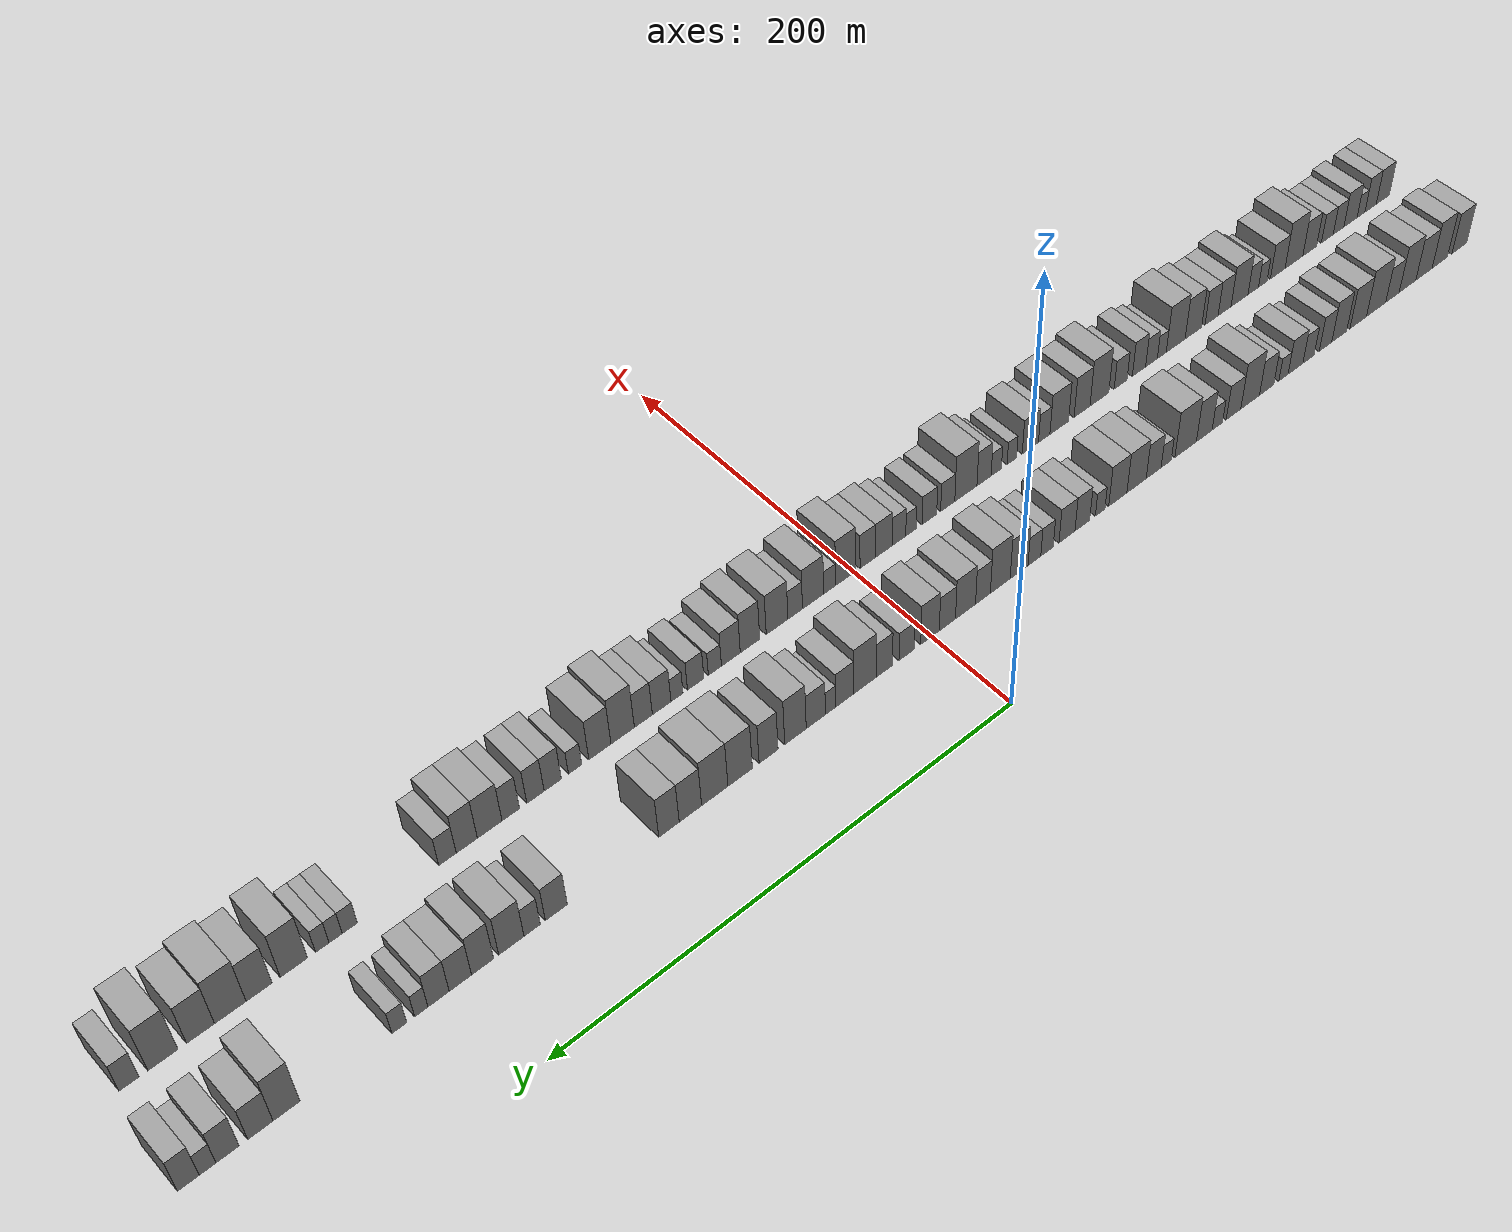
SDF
<sdf version="1.6">
 <world name="default">
  <scene>
   <sky><clouds><speed>12</speed></clouds></sky>
   <ambient>0.4 0.4 0.4 1</ambient>
   <background>0.7 0.7 0.7 1</background>
   <shadows>1</shadows>
  </scene>
  <gravity>0 0 -9.8066</gravity>
  <magnetic_field>6e-06 2.3e-05 -4.2e-05</magnetic_field>
  <physics default="0" name="default_physics" type="ode">
   <ode>
    <solver>
     <type>quick</type>
     <iters>10</iters>
     <sor>1.0</sor>
     <use_dynamic_moi_rescaling>0</use_dynamic_moi_rescaling>
    </solver>
    <constraints>
     <cfm>0</cfm>
     <erp>0.2</erp>
     <contact_max_correcting_vel>100</contact_max_correcting_vel>
     <contact_surface_layer>0.001</contact_surface_layer>
    </constraints>
   </ode>
   <max_step_size>0.004</max_step_size>
   <real_time_factor>1</real_time_factor>
   <real_time_update_rate>250</real_time_update_rate>
  </physics>
  <light name="sun" type="directional">
   <pose>0 0 10 0 0 0</pose>
   <diffuse>0.8 0.8 0.8 1</diffuse>
   <specular>0.2 0.2 0.2 1</specular>
   <attenuation>
    <range>1000</range>
    <constant>0.9</constant>
    <linear>0.01</linear>
    <quadratic>0.001</quadratic>
   </attenuation>
   <direction>-0.5 0.1 -0.9</direction>
  </light>
  <model name="building_1">
   <static>1</static>
   <pose>50.0000 -295.3019 0 0.000000 0.000000 0.000000</pose>
   <link name="link">
    <pose>0 0 10.50 0 0 0</pose>
    <collision name="collision"><geometry><box><size>20.0000 9.3963 21.0000</size></box></geometry></collision>
    <visual name="visual">
     <cast_shadows>0</cast_shadows>
     <geometry><box><size>20.0000 9.3963 21.0000</size></box></geometry>
     <material>
      <script>
       <uri>model://grey_wall/materials/scripts</uri>
       <uri>model://grey_wall/materials/textures</uri>
       <name>vrc/grey_wall</name>
      </script>
     </material>
    </visual>
   </link>
  </model>
  <model name="building_2">
   <static>1</static>
   <pose>50.0000 -282.7249 0 0.000000 0.000000 0.000000</pose>
   <link name="link">
    <pose>0 0 12.00 0 0 0</pose>
    <collision name="collision"><geometry><box><size>20.0000 9.7576 24.0000</size></box></geometry></collision>
    <visual name="visual">
     <cast_shadows>0</cast_shadows>
     <geometry><box><size>20.0000 9.7576 24.0000</size></box></geometry>
     <material>
      <script>
       <uri>model://grey_wall/materials/scripts</uri>
       <uri>model://grey_wall/materials/textures</uri>
       <name>vrc/grey_wall</name>
      </script>
     </material>
    </visual>
   </link>
  </model>
  <model name="building_3">
   <static>1</static>
   <pose>50.0000 -272.7034 0 0.000000 0.000000 0.000000</pose>
   <link name="link">
    <pose>0 0 10.50 0 0 0</pose>
    <collision name="collision"><geometry><box><size>20.0000 10.2854 21.0000</size></box></geometry></collision>
    <visual name="visual">
     <cast_shadows>0</cast_shadows>
     <geometry><box><size>20.0000 10.2854 21.0000</size></box></geometry>
     <material>
      <script>
       <uri>model://grey_wall/materials/scripts</uri>
       <uri>model://grey_wall/materials/textures</uri>
       <name>vrc/grey_wall</name>
      </script>
     </material>
    </visual>
   </link>
  </model>
  <model name="building_4">
   <static>1</static>
   <pose>50.0000 -262.3470 0 0.000000 0.000000 0.000000</pose>
   <link name="link">
    <pose>0 0 12.00 0 0 0</pose>
    <collision name="collision"><geometry><box><size>20.0000 10.4274 24.0000</size></box></geometry></collision>
    <visual name="visual">
     <cast_shadows>0</cast_shadows>
     <geometry><box><size>20.0000 10.4274 24.0000</size></box></geometry>
     <material>
      <script>
       <uri>model://grey_wall/materials/scripts</uri>
       <uri>model://grey_wall/materials/textures</uri>
       <name>vrc/grey_wall</name>
      </script>
     </material>
    </visual>
   </link>
  </model>
  <model name="building_5">
   <static>1</static>
   <pose>50.0000 -252.9480 0 0.000000 0.000000 0.000000</pose>
   <link name="link">
    <pose>0 0 9.00 0 0 0</pose>
    <collision name="collision"><geometry><box><size>20.0000 8.3706 18.0000</size></box></geometry></collision>
    <visual name="visual">
     <cast_shadows>0</cast_shadows>
     <geometry><box><size>20.0000 8.3706 18.0000</size></box></geometry>
     <material>
      <script>
       <uri>model://grey_wall/materials/scripts</uri>
       <uri>model://grey_wall/materials/textures</uri>
       <name>vrc/grey_wall</name>
      </script>
     </material>
    </visual>
   </link>
  </model>
  <model name="building_6">
   <static>1</static>
   <pose>50.0000 -242.8675 0 0.000000 0.000000 0.000000</pose>
   <link name="link">
    <pose>0 0 12.00 0 0 0</pose>
    <collision name="collision"><geometry><box><size>20.0000 11.7904 24.0000</size></box></geometry></collision>
    <visual name="visual">
     <cast_shadows>0</cast_shadows>
     <geometry><box><size>20.0000 11.7904 24.0000</size></box></geometry>
     <material>
      <script>
       <uri>model://grey_wall/materials/scripts</uri>
       <uri>model://grey_wall/materials/textures</uri>
       <name>vrc/grey_wall</name>
      </script>
     </material>
    </visual>
   </link>
  </model>
  <model name="building_7">
   <static>1</static>
   <pose>50.0000 -231.9022 0 0.000000 0.000000 0.000000</pose>
   <link name="link">
    <pose>0 0 10.50 0 0 0</pose>
    <collision name="collision"><geometry><box><size>20.0000 10.1402 21.0000</size></box></geometry></collision>
    <visual name="visual">
     <cast_shadows>0</cast_shadows>
     <geometry><box><size>20.0000 10.1402 21.0000</size></box></geometry>
     <material>
      <script>
       <uri>model://grey_wall/materials/scripts</uri>
       <uri>model://grey_wall/materials/textures</uri>
       <name>vrc/grey_wall</name>
      </script>
     </material>
    </visual>
   </link>
  </model>
  <model name="building_8">
   <static>1</static>
   <pose>50.0000 -220.3504 0 0.000000 0.000000 0.000000</pose>
   <link name="link">
    <pose>0 0 10.50 0 0 0</pose>
    <collision name="collision"><geometry><box><size>20.0000 8.9634 21.0000</size></box></geometry></collision>
    <visual name="visual">
     <cast_shadows>0</cast_shadows>
     <geometry><box><size>20.0000 8.9634 21.0000</size></box></geometry>
     <material>
      <script>
       <uri>model://grey_wall/materials/scripts</uri>
       <uri>model://grey_wall/materials/textures</uri>
       <name>vrc/grey_wall</name>
      </script>
     </material>
    </visual>
   </link>
  </model>
  <model name="building_9">
   <static>1</static>
   <pose>50.0000 -212.1136 0 0.000000 0.000000 0.000000</pose>
   <link name="link">
    <pose>0 0 9.00 0 0 0</pose>
    <collision name="collision"><geometry><box><size>20.0000 7.5102 18.0000</size></box></geometry></collision>
    <visual name="visual">
     <cast_shadows>0</cast_shadows>
     <geometry><box><size>20.0000 7.5102 18.0000</size></box></geometry>
     <material>
      <script>
       <uri>model://grey_wall/materials/scripts</uri>
       <uri>model://grey_wall/materials/textures</uri>
       <name>vrc/grey_wall</name>
      </script>
     </material>
    </visual>
   </link>
  </model>
  <model name="building_10">
   <static>1</static>
   <pose>50.0000 -202.0355 0 0.000000 0.000000 0.000000</pose>
   <link name="link">
    <pose>0 0 7.50 0 0 0</pose>
    <collision name="collision"><geometry><box><size>20.0000 6.6459 15.0000</size></box></geometry></collision>
    <visual name="visual">
     <cast_shadows>0</cast_shadows>
     <geometry><box><size>20.0000 6.6459 15.0000</size></box></geometry>
     <material>
      <script>
       <uri>model://grey_wall/materials/scripts</uri>
       <uri>model://grey_wall/materials/textures</uri>
       <name>vrc/grey_wall</name>
      </script>
     </material>
    </visual>
   </link>
  </model>
  <model name="building_11">
   <static>1</static>
   <pose>50.0000 -194.3298 0 0.000000 0.000000 0.000000</pose>
   <link name="link">
    <pose>0 0 9.00 0 0 0</pose>
    <collision name="collision"><geometry><box><size>20.0000 8.7655 18.0000</size></box></geometry></collision>
    <visual name="visual">
     <cast_shadows>0</cast_shadows>
     <geometry><box><size>20.0000 8.7655 18.0000</size></box></geometry>
     <material>
      <script>
       <uri>model://grey_wall/materials/scripts</uri>
       <uri>model://grey_wall/materials/textures</uri>
       <name>vrc/grey_wall</name>
      </script>
     </material>
    </visual>
   </link>
  </model>
  <model name="building_12">
   <static>1</static>
   <pose>50.0000 -187.2509 0 0.000000 0.000000 0.000000</pose>
   <link name="link">
    <pose>0 0 6.00 0 0 0</pose>
    <collision name="collision"><geometry><box><size>20.0000 5.3923 12.0000</size></box></geometry></collision>
    <visual name="visual">
     <cast_shadows>0</cast_shadows>
     <geometry><box><size>20.0000 5.3923 12.0000</size></box></geometry>
     <material>
      <script>
       <uri>model://grey_wall/materials/scripts</uri>
       <uri>model://grey_wall/materials/textures</uri>
       <name>vrc/grey_wall</name>
      </script>
     </material>
    </visual>
   </link>
  </model>
  <model name="building_13">
   <static>1</static>
   <pose>50.0000 -177.4368 0 0.000000 0.000000 0.000000</pose>
   <link name="link">
    <pose>0 0 9.00 0 0 0</pose>
    <collision name="collision"><geometry><box><size>20.0000 8.2360 18.0000</size></box></geometry></collision>
    <visual name="visual">
     <cast_shadows>0</cast_shadows>
     <geometry><box><size>20.0000 8.2360 18.0000</size></box></geometry>
     <material>
      <script>
       <uri>model://grey_wall/materials/scripts</uri>
       <uri>model://grey_wall/materials/textures</uri>
       <name>vrc/grey_wall</name>
      </script>
     </material>
    </visual>
   </link>
  </model>
  <model name="building_14">
   <static>1</static>
   <pose>50.0000 -167.9649 0 0.000000 0.000000 0.000000</pose>
   <link name="link">
    <pose>0 0 12.00 0 0 0</pose>
    <collision name="collision"><geometry><box><size>20.0000 10.7077 24.0000</size></box></geometry></collision>
    <visual name="visual">
     <cast_shadows>0</cast_shadows>
     <geometry><box><size>20.0000 10.7077 24.0000</size></box></geometry>
     <material>
      <script>
       <uri>model://grey_wall/materials/scripts</uri>
       <uri>model://grey_wall/materials/textures</uri>
       <name>vrc/grey_wall</name>
      </script>
     </material>
    </visual>
   </link>
  </model>
  <model name="building_15">
   <static>1</static>
   <pose>50.0000 -158.4264 0 0.000000 0.000000 0.000000</pose>
   <link name="link">
    <pose>0 0 9.00 0 0 0</pose>
    <collision name="collision"><geometry><box><size>20.0000 8.3694 18.0000</size></box></geometry></collision>
    <visual name="visual">
     <cast_shadows>0</cast_shadows>
     <geometry><box><size>20.0000 8.3694 18.0000</size></box></geometry>
     <material>
      <script>
       <uri>model://grey_wall/materials/scripts</uri>
       <uri>model://grey_wall/materials/textures</uri>
       <name>vrc/grey_wall</name>
      </script>
     </material>
    </visual>
   </link>
  </model>
  <model name="building_16">
   <static>1</static>
   <pose>50.0000 -149.3047 0 0.000000 0.000000 0.000000</pose>
   <link name="link">
    <pose>0 0 6.00 0 0 0</pose>
    <collision name="collision"><geometry><box><size>20.0000 5.8741 12.0000</size></box></geometry></collision>
    <visual name="visual">
     <cast_shadows>0</cast_shadows>
     <geometry><box><size>20.0000 5.8741 12.0000</size></box></geometry>
     <material>
      <script>
       <uri>model://grey_wall/materials/scripts</uri>
       <uri>model://grey_wall/materials/textures</uri>
       <name>vrc/grey_wall</name>
      </script>
     </material>
    </visual>
   </link>
  </model>
  <model name="building_17">
   <static>1</static>
   <pose>50.0000 -141.9949 0 0.000000 0.000000 0.000000</pose>
   <link name="link">
    <pose>0 0 10.50 0 0 0</pose>
    <collision name="collision"><geometry><box><size>20.0000 8.7454 21.0000</size></box></geometry></collision>
    <visual name="visual">
     <cast_shadows>0</cast_shadows>
     <geometry><box><size>20.0000 8.7454 21.0000</size></box></geometry>
     <material>
      <script>
       <uri>model://grey_wall/materials/scripts</uri>
       <uri>model://grey_wall/materials/textures</uri>
       <name>vrc/grey_wall</name>
      </script>
     </material>
    </visual>
   </link>
  </model>
  <model name="building_18">
   <static>1</static>
   <pose>50.0000 -131.6551 0 0.000000 0.000000 0.000000</pose>
   <link name="link">
    <pose>0 0 12.00 0 0 0</pose>
    <collision name="collision"><geometry><box><size>20.0000 11.9344 24.0000</size></box></geometry></collision>
    <visual name="visual">
     <cast_shadows>0</cast_shadows>
     <geometry><box><size>20.0000 11.9344 24.0000</size></box></geometry>
     <material>
      <script>
       <uri>model://grey_wall/materials/scripts</uri>
       <uri>model://grey_wall/materials/textures</uri>
       <name>vrc/grey_wall</name>
      </script>
     </material>
    </visual>
   </link>
  </model>
  <model name="building_19">
   <static>1</static>
   <pose>50.0000 -120.9007 0 0.000000 0.000000 0.000000</pose>
   <link name="link">
    <pose>0 0 6.00 0 0 0</pose>
    <collision name="collision"><geometry><box><size>20.0000 5.5743 12.0000</size></box></geometry></collision>
    <visual name="visual">
     <cast_shadows>0</cast_shadows>
     <geometry><box><size>20.0000 5.5743 12.0000</size></box></geometry>
     <material>
      <script>
       <uri>model://grey_wall/materials/scripts</uri>
       <uri>model://grey_wall/materials/textures</uri>
       <name>vrc/grey_wall</name>
      </script>
     </material>
    </visual>
   </link>
  </model>
  <model name="building_20">
   <static>1</static>
   <pose>50.0000 -114.0491 0 0.000000 0.000000 0.000000</pose>
   <link name="link">
    <pose>0 0 9.00 0 0 0</pose>
    <collision name="collision"><geometry><box><size>20.0000 8.1289 18.0000</size></box></geometry></collision>
    <visual name="visual">
     <cast_shadows>0</cast_shadows>
     <geometry><box><size>20.0000 8.1289 18.0000</size></box></geometry>
     <material>
      <script>
       <uri>model://grey_wall/materials/scripts</uri>
       <uri>model://grey_wall/materials/textures</uri>
       <name>vrc/grey_wall</name>
      </script>
     </material>
    </visual>
   </link>
  </model>
  <model name="building_21">
   <static>1</static>
   <pose>50.0000 -104.8026 0 0.000000 0.000000 0.000000</pose>
   <link name="link">
    <pose>0 0 10.50 0 0 0</pose>
    <collision name="collision"><geometry><box><size>20.0000 10.3641 21.0000</size></box></geometry></collision>
    <visual name="visual">
     <cast_shadows>0</cast_shadows>
     <geometry><box><size>20.0000 10.3641 21.0000</size></box></geometry>
     <material>
      <script>
       <uri>model://grey_wall/materials/scripts</uri>
       <uri>model://grey_wall/materials/textures</uri>
       <name>vrc/grey_wall</name>
      </script>
     </material>
    </visual>
   </link>
  </model>
  <model name="building_22">
   <static>1</static>
   <pose>50.0000 -94.7582 0 0.000000 0.000000 0.000000</pose>
   <link name="link">
    <pose>0 0 10.50 0 0 0</pose>
    <collision name="collision"><geometry><box><size>20.0000 9.7247 21.0000</size></box></geometry></collision>
    <visual name="visual">
     <cast_shadows>0</cast_shadows>
     <geometry><box><size>20.0000 9.7247 21.0000</size></box></geometry>
     <material>
      <script>
       <uri>model://grey_wall/materials/scripts</uri>
       <uri>model://grey_wall/materials/textures</uri>
       <name>vrc/grey_wall</name>
      </script>
     </material>
    </visual>
   </link>
  </model>
  <model name="building_23">
   <static>1</static>
   <pose>50.0000 -85.3708 0 0.000000 0.000000 0.000000</pose>
   <link name="link">
    <pose>0 0 6.00 0 0 0</pose>
    <collision name="collision"><geometry><box><size>20.0000 5.0501 12.0000</size></box></geometry></collision>
    <visual name="visual">
     <cast_shadows>0</cast_shadows>
     <geometry><box><size>20.0000 5.0501 12.0000</size></box></geometry>
     <material>
      <script>
       <uri>model://grey_wall/materials/scripts</uri>
       <uri>model://grey_wall/materials/textures</uri>
       <name>vrc/grey_wall</name>
      </script>
     </material>
    </visual>
   </link>
  </model>
  <model name="building_24">
   <static>1</static>
   <pose>50.0000 -76.0046 0 0.000000 0.000000 0.000000</pose>
   <link name="link">
    <pose>0 0 9.00 0 0 0</pose>
    <collision name="collision"><geometry><box><size>20.0000 7.6823 18.0000</size></box></geometry></collision>
    <visual name="visual">
     <cast_shadows>0</cast_shadows>
     <geometry><box><size>20.0000 7.6823 18.0000</size></box></geometry>
     <material>
      <script>
       <uri>model://grey_wall/materials/scripts</uri>
       <uri>model://grey_wall/materials/textures</uri>
       <name>vrc/grey_wall</name>
      </script>
     </material>
    </visual>
   </link>
  </model>
  <model name="building_25">
   <static>1</static>
   <pose>50.0000 -68.0026 0 0.000000 0.000000 0.000000</pose>
   <link name="link">
    <pose>0 0 9.00 0 0 0</pose>
    <collision name="collision"><geometry><box><size>20.0000 8.3216 18.0000</size></box></geometry></collision>
    <visual name="visual">
     <cast_shadows>0</cast_shadows>
     <geometry><box><size>20.0000 8.3216 18.0000</size></box></geometry>
     <material>
      <script>
       <uri>model://grey_wall/materials/scripts</uri>
       <uri>model://grey_wall/materials/textures</uri>
       <name>vrc/grey_wall</name>
      </script>
     </material>
    </visual>
   </link>
  </model>
  <model name="building_26">
   <static>1</static>
   <pose>50.0000 -57.6527 0 0.000000 0.000000 0.000000</pose>
   <link name="link">
    <pose>0 0 7.50 0 0 0</pose>
    <collision name="collision"><geometry><box><size>20.0000 6.3781 15.0000</size></box></geometry></collision>
    <visual name="visual">
     <cast_shadows>0</cast_shadows>
     <geometry><box><size>20.0000 6.3781 15.0000</size></box></geometry>
     <material>
      <script>
       <uri>model://grey_wall/materials/scripts</uri>
       <uri>model://grey_wall/materials/textures</uri>
       <name>vrc/grey_wall</name>
      </script>
     </material>
    </visual>
   </link>
  </model>
  <model name="building_27">
   <static>1</static>
   <pose>50.0000 -51.2100 0 0.000000 0.000000 0.000000</pose>
   <link name="link">
    <pose>0 0 7.50 0 0 0</pose>
    <collision name="collision"><geometry><box><size>20.0000 6.5072 15.0000</size></box></geometry></collision>
    <visual name="visual">
     <cast_shadows>0</cast_shadows>
     <geometry><box><size>20.0000 6.5072 15.0000</size></box></geometry>
     <material>
      <script>
       <uri>model://grey_wall/materials/scripts</uri>
       <uri>model://grey_wall/materials/textures</uri>
       <name>vrc/grey_wall</name>
      </script>
     </material>
    </visual>
   </link>
  </model>
  <model name="building_28">
   <static>1</static>
   <pose>50.0000 -43.4362 0 0.000000 0.000000 0.000000</pose>
   <link name="link">
    <pose>0 0 10.50 0 0 0</pose>
    <collision name="collision"><geometry><box><size>20.0000 9.0404 21.0000</size></box></geometry></collision>
    <visual name="visual">
     <cast_shadows>0</cast_shadows>
     <geometry><box><size>20.0000 9.0404 21.0000</size></box></geometry>
     <material>
      <script>
       <uri>model://grey_wall/materials/scripts</uri>
       <uri>model://grey_wall/materials/textures</uri>
       <name>vrc/grey_wall</name>
      </script>
     </material>
    </visual>
   </link>
  </model>
  <model name="building_29">
   <static>1</static>
   <pose>50.0000 -33.9522 0 0.000000 0.000000 0.000000</pose>
   <link name="link">
    <pose>0 0 12.00 0 0 0</pose>
    <collision name="collision"><geometry><box><size>20.0000 9.9278 24.0000</size></box></geometry></collision>
    <visual name="visual">
     <cast_shadows>0</cast_shadows>
     <geometry><box><size>20.0000 9.9278 24.0000</size></box></geometry>
     <material>
      <script>
       <uri>model://grey_wall/materials/scripts</uri>
       <uri>model://grey_wall/materials/textures</uri>
       <name>vrc/grey_wall</name>
      </script>
     </material>
    </visual>
   </link>
  </model>
  <model name="building_30">
   <static>1</static>
   <pose>50.0000 -25.3044 0 0.000000 0.000000 0.000000</pose>
   <link name="link">
    <pose>0 0 9.00 0 0 0</pose>
    <collision name="collision"><geometry><box><size>20.0000 7.3676 18.0000</size></box></geometry></collision>
    <visual name="visual">
     <cast_shadows>0</cast_shadows>
     <geometry><box><size>20.0000 7.3676 18.0000</size></box></geometry>
     <material>
      <script>
       <uri>model://grey_wall/materials/scripts</uri>
       <uri>model://grey_wall/materials/textures</uri>
       <name>vrc/grey_wall</name>
      </script>
     </material>
    </visual>
   </link>
  </model>
  <model name="building_31">
   <static>1</static>
   <pose>50.0000 -16.6911 0 0.000000 0.000000 0.000000</pose>
   <link name="link">
    <pose>0 0 10.50 0 0 0</pose>
    <collision name="collision"><geometry><box><size>20.0000 9.8591 21.0000</size></box></geometry></collision>
    <visual name="visual">
     <cast_shadows>0</cast_shadows>
     <geometry><box><size>20.0000 9.8591 21.0000</size></box></geometry>
     <material>
      <script>
       <uri>model://grey_wall/materials/scripts</uri>
       <uri>model://grey_wall/materials/textures</uri>
       <name>vrc/grey_wall</name>
      </script>
     </material>
    </visual>
   </link>
  </model>
  <model name="building_32">
   <static>1</static>
   <pose>50.0000 -7.8064 0 0.000000 0.000000 0.000000</pose>
   <link name="link">
    <pose>0 0 9.00 0 0 0</pose>
    <collision name="collision"><geometry><box><size>20.0000 7.9102 18.0000</size></box></geometry></collision>
    <visual name="visual">
     <cast_shadows>0</cast_shadows>
     <geometry><box><size>20.0000 7.9102 18.0000</size></box></geometry>
     <material>
      <script>
       <uri>model://grey_wall/materials/scripts</uri>
       <uri>model://grey_wall/materials/textures</uri>
       <name>vrc/grey_wall</name>
      </script>
     </material>
    </visual>
   </link>
  </model>
  <model name="building_33">
   <static>1</static>
   <pose>50.0000 0.6344 0 0.000000 0.000000 0.000000</pose>
   <link name="link">
    <pose>0 0 10.50 0 0 0</pose>
    <collision name="collision"><geometry><box><size>20.0000 8.9715 21.0000</size></box></geometry></collision>
    <visual name="visual">
     <cast_shadows>0</cast_shadows>
     <geometry><box><size>20.0000 8.9715 21.0000</size></box></geometry>
     <material>
      <script>
       <uri>model://grey_wall/materials/scripts</uri>
       <uri>model://grey_wall/materials/textures</uri>
       <name>vrc/grey_wall</name>
      </script>
     </material>
    </visual>
   </link>
  </model>
  <model name="building_34">
   <static>1</static>
   <pose>50.0000 11.8369 0 0.000000 0.000000 0.000000</pose>
   <link name="link">
    <pose>0 0 7.50 0 0 0</pose>
    <collision name="collision"><geometry><box><size>20.0000 7.4334 15.0000</size></box></geometry></collision>
    <visual name="visual">
     <cast_shadows>0</cast_shadows>
     <geometry><box><size>20.0000 7.4334 15.0000</size></box></geometry>
     <material>
      <script>
       <uri>model://grey_wall/materials/scripts</uri>
       <uri>model://grey_wall/materials/textures</uri>
       <name>vrc/grey_wall</name>
      </script>
     </material>
    </visual>
   </link>
  </model>
  <model name="building_35">
   <static>1</static>
   <pose>50.0000 22.2946 0 0.000000 0.000000 0.000000</pose>
   <link name="link">
    <pose>0 0 9.00 0 0 0</pose>
    <collision name="collision"><geometry><box><size>20.0000 7.4822 18.0000</size></box></geometry></collision>
    <visual name="visual">
     <cast_shadows>0</cast_shadows>
     <geometry><box><size>20.0000 7.4822 18.0000</size></box></geometry>
     <material>
      <script>
       <uri>model://grey_wall/materials/scripts</uri>
       <uri>model://grey_wall/materials/textures</uri>
       <name>vrc/grey_wall</name>
      </script>
     </material>
    </visual>
   </link>
  </model>
  <model name="building_36">
   <static>1</static>
   <pose>50.0000 31.4250 0 0.000000 0.000000 0.000000</pose>
   <link name="link">
    <pose>0 0 12.00 0 0 0</pose>
    <collision name="collision"><geometry><box><size>20.0000 10.7786 24.0000</size></box></geometry></collision>
    <visual name="visual">
     <cast_shadows>0</cast_shadows>
     <geometry><box><size>20.0000 10.7786 24.0000</size></box></geometry>
     <material>
      <script>
       <uri>model://grey_wall/materials/scripts</uri>
       <uri>model://grey_wall/materials/textures</uri>
       <name>vrc/grey_wall</name>
      </script>
     </material>
    </visual>
   </link>
  </model>
  <model name="building_37">
   <static>1</static>
   <pose>50.0000 40.9600 0 0.000000 0.000000 0.000000</pose>
   <link name="link">
    <pose>0 0 9.00 0 0 0</pose>
    <collision name="collision"><geometry><box><size>20.0000 8.2913 18.0000</size></box></geometry></collision>
    <visual name="visual">
     <cast_shadows>0</cast_shadows>
     <geometry><box><size>20.0000 8.2913 18.0000</size></box></geometry>
     <material>
      <script>
       <uri>model://grey_wall/materials/scripts</uri>
       <uri>model://grey_wall/materials/textures</uri>
       <name>vrc/grey_wall</name>
      </script>
     </material>
    </visual>
   </link>
  </model>
  <model name="building_38">
   <static>1</static>
   <pose>50.0000 47.5080 0 0.000000 0.000000 0.000000</pose>
   <link name="link">
    <pose>0 0 6.00 0 0 0</pose>
    <collision name="collision"><geometry><box><size>20.0000 4.8046 12.0000</size></box></geometry></collision>
    <visual name="visual">
     <cast_shadows>0</cast_shadows>
     <geometry><box><size>20.0000 4.8046 12.0000</size></box></geometry>
     <material>
      <script>
       <uri>model://grey_wall/materials/scripts</uri>
       <uri>model://grey_wall/materials/textures</uri>
       <name>vrc/grey_wall</name>
      </script>
     </material>
    </visual>
   </link>
  </model>
  <model name="building_39">
   <static>1</static>
   <pose>50.0000 54.3038 0 0.000000 0.000000 0.000000</pose>
   <link name="link">
    <pose>0 0 9.00 0 0 0</pose>
    <collision name="collision"><geometry><box><size>20.0000 8.7870 18.0000</size></box></geometry></collision>
    <visual name="visual">
     <cast_shadows>0</cast_shadows>
     <geometry><box><size>20.0000 8.7870 18.0000</size></box></geometry>
     <material>
      <script>
       <uri>model://grey_wall/materials/scripts</uri>
       <uri>model://grey_wall/materials/textures</uri>
       <name>vrc/grey_wall</name>
      </script>
     </material>
    </visual>
   </link>
  </model>
  <model name="building_40">
   <static>1</static>
   <pose>50.0000 63.5560 0 0.000000 0.000000 0.000000</pose>
   <link name="link">
    <pose>0 0 12.00 0 0 0</pose>
    <collision name="collision"><geometry><box><size>20.0000 9.7173 24.0000</size></box></geometry></collision>
    <visual name="visual">
     <cast_shadows>0</cast_shadows>
     <geometry><box><size>20.0000 9.7173 24.0000</size></box></geometry>
     <material>
      <script>
       <uri>model://grey_wall/materials/scripts</uri>
       <uri>model://grey_wall/materials/textures</uri>
       <name>vrc/grey_wall</name>
      </script>
     </material>
    </visual>
   </link>
  </model>
  <model name="building_41">
   <static>1</static>
   <pose>50.0000 75.6388 0 0.000000 0.000000 0.000000</pose>
   <link name="link">
    <pose>0 0 10.50 0 0 0</pose>
    <collision name="collision"><geometry><box><size>20.0000 8.4484 21.0000</size></box></geometry></collision>
    <visual name="visual">
     <cast_shadows>0</cast_shadows>
     <geometry><box><size>20.0000 8.4484 21.0000</size></box></geometry>
     <material>
      <script>
       <uri>model://grey_wall/materials/scripts</uri>
       <uri>model://grey_wall/materials/textures</uri>
       <name>vrc/grey_wall</name>
      </script>
     </material>
    </visual>
   </link>
  </model>
  <model name="building_42">
   <static>1</static>
   <pose>50.0000 88.2339 0 0.000000 0.000000 0.000000</pose>
   <link name="link">
    <pose>0 0 12.00 0 0 0</pose>
    <collision name="collision"><geometry><box><size>20.0000 10.7418 24.0000</size></box></geometry></collision>
    <visual name="visual">
     <cast_shadows>0</cast_shadows>
     <geometry><box><size>20.0000 10.7418 24.0000</size></box></geometry>
     <material>
      <script>
       <uri>model://grey_wall/materials/scripts</uri>
       <uri>model://grey_wall/materials/textures</uri>
       <name>vrc/grey_wall</name>
      </script>
     </material>
    </visual>
   </link>
  </model>
  <model name="building_43">
   <static>1</static>
   <pose>50.0000 99.3218 0 0.000000 0.000000 0.000000</pose>
   <link name="link">
    <pose>0 0 12.00 0 0 0</pose>
    <collision name="collision"><geometry><box><size>20.0000 11.4338 24.0000</size></box></geometry></collision>
    <visual name="visual">
     <cast_shadows>0</cast_shadows>
     <geometry><box><size>20.0000 11.4338 24.0000</size></box></geometry>
     <material>
      <script>
       <uri>model://grey_wall/materials/scripts</uri>
       <uri>model://grey_wall/materials/textures</uri>
       <name>vrc/grey_wall</name>
      </script>
     </material>
    </visual>
   </link>
  </model>
  <model name="building_44">
   <static>1</static>
   <pose>50.0000 109.8628 0 0.000000 0.000000 0.000000</pose>
   <link name="link">
    <pose>0 0 10.50 0 0 0</pose>
    <collision name="collision"><geometry><box><size>20.0000 9.6482 21.0000</size></box></geometry></collision>
    <visual name="visual">
     <cast_shadows>0</cast_shadows>
     <geometry><box><size>20.0000 9.6482 21.0000</size></box></geometry>
     <material>
      <script>
       <uri>model://grey_wall/materials/scripts</uri>
       <uri>model://grey_wall/materials/textures</uri>
       <name>vrc/grey_wall</name>
      </script>
     </material>
    </visual>
   </link>
  </model>
  <model name="building_45">
   <static>1</static>
   <pose>50.0000 119.0408 0 0.000000 0.000000 0.000000</pose>
   <link name="link">
    <pose>0 0 10.50 0 0 0</pose>
    <collision name="collision"><geometry><box><size>20.0000 8.7080 21.0000</size></box></geometry></collision>
    <visual name="visual">
     <cast_shadows>0</cast_shadows>
     <geometry><box><size>20.0000 8.7080 21.0000</size></box></geometry>
     <material>
      <script>
       <uri>model://grey_wall/materials/scripts</uri>
       <uri>model://grey_wall/materials/textures</uri>
       <name>vrc/grey_wall</name>
      </script>
     </material>
    </visual>
   </link>
  </model>
  <model name="building_46">
   <static>1</static>
   <pose>50.0000 165.6891 0 0.000000 0.000000 0.000000</pose>
   <link name="link">
    <pose>0 0 9.00 0 0 0</pose>
    <collision name="collision"><geometry><box><size>20.0000 8.8628 18.0000</size></box></geometry></collision>
    <visual name="visual">
     <cast_shadows>0</cast_shadows>
     <geometry><box><size>20.0000 8.8628 18.0000</size></box></geometry>
     <material>
      <script>
       <uri>model://grey_wall/materials/scripts</uri>
       <uri>model://grey_wall/materials/textures</uri>
       <name>vrc/grey_wall</name>
      </script>
     </material>
    </visual>
   </link>
  </model>
  <model name="building_47">
   <static>1</static>
   <pose>50.0000 175.3788 0 0.000000 0.000000 0.000000</pose>
   <link name="link">
    <pose>0 0 7.50 0 0 0</pose>
    <collision name="collision"><geometry><box><size>20.0000 6.5166 15.0000</size></box></geometry></collision>
    <visual name="visual">
     <cast_shadows>0</cast_shadows>
     <geometry><box><size>20.0000 6.5166 15.0000</size></box></geometry>
     <material>
      <script>
       <uri>model://grey_wall/materials/scripts</uri>
       <uri>model://grey_wall/materials/textures</uri>
       <name>vrc/grey_wall</name>
      </script>
     </material>
    </visual>
   </link>
  </model>
  <model name="building_48">
   <static>1</static>
   <pose>50.0000 183.6263 0 0.000000 0.000000 0.000000</pose>
   <link name="link">
    <pose>0 0 10.50 0 0 0</pose>
    <collision name="collision"><geometry><box><size>20.0000 9.9783 21.0000</size></box></geometry></collision>
    <visual name="visual">
     <cast_shadows>0</cast_shadows>
     <geometry><box><size>20.0000 9.9783 21.0000</size></box></geometry>
     <material>
      <script>
       <uri>model://grey_wall/materials/scripts</uri>
       <uri>model://grey_wall/materials/textures</uri>
       <name>vrc/grey_wall</name>
      </script>
     </material>
    </visual>
   </link>
  </model>
  <model name="building_49">
   <static>1</static>
   <pose>50.0000 194.9066 0 0.000000 0.000000 0.000000</pose>
   <link name="link">
    <pose>0 0 10.50 0 0 0</pose>
    <collision name="collision"><geometry><box><size>20.0000 8.5822 21.0000</size></box></geometry></collision>
    <visual name="visual">
     <cast_shadows>0</cast_shadows>
     <geometry><box><size>20.0000 8.5822 21.0000</size></box></geometry>
     <material>
      <script>
       <uri>model://grey_wall/materials/scripts</uri>
       <uri>model://grey_wall/materials/textures</uri>
       <name>vrc/grey_wall</name>
      </script>
     </material>
    </visual>
   </link>
  </model>
  <model name="building_50">
   <static>1</static>
   <pose>50.0000 203.5195 0 0.000000 0.000000 0.000000</pose>
   <link name="link">
    <pose>0 0 9.00 0 0 0</pose>
    <collision name="collision"><geometry><box><size>20.0000 8.6437 18.0000</size></box></geometry></collision>
    <visual name="visual">
     <cast_shadows>0</cast_shadows>
     <geometry><box><size>20.0000 8.6437 18.0000</size></box></geometry>
     <material>
      <script>
       <uri>model://grey_wall/materials/scripts</uri>
       <uri>model://grey_wall/materials/textures</uri>
       <name>vrc/grey_wall</name>
      </script>
     </material>
    </visual>
   </link>
  </model>
  <model name="building_51">
   <static>1</static>
   <pose>50.0000 211.8995 0 0.000000 0.000000 0.000000</pose>
   <link name="link">
    <pose>0 0 9.00 0 0 0</pose>
    <collision name="collision"><geometry><box><size>20.0000 8.1161 18.0000</size></box></geometry></collision>
    <visual name="visual">
     <cast_shadows>0</cast_shadows>
     <geometry><box><size>20.0000 8.1161 18.0000</size></box></geometry>
     <material>
      <script>
       <uri>model://grey_wall/materials/scripts</uri>
       <uri>model://grey_wall/materials/textures</uri>
       <name>vrc/grey_wall</name>
      </script>
     </material>
    </visual>
   </link>
  </model>
  <model name="building_52">
   <static>1</static>
   <pose>50.0000 218.4815 0 0.000000 0.000000 0.000000</pose>
   <link name="link">
    <pose>0 0 6.00 0 0 0</pose>
    <collision name="collision"><geometry><box><size>20.0000 5.0480 12.0000</size></box></geometry></collision>
    <visual name="visual">
     <cast_shadows>0</cast_shadows>
     <geometry><box><size>20.0000 5.0480 12.0000</size></box></geometry>
     <material>
      <script>
       <uri>model://grey_wall/materials/scripts</uri>
       <uri>model://grey_wall/materials/textures</uri>
       <name>vrc/grey_wall</name>
      </script>
     </material>
    </visual>
   </link>
  </model>
  <model name="building_53">
   <static>1</static>
   <pose>50.0000 226.8171 0 0.000000 0.000000 0.000000</pose>
   <link name="link">
    <pose>0 0 6.00 0 0 0</pose>
    <collision name="collision"><geometry><box><size>20.0000 5.6231 12.0000</size></box></geometry></collision>
    <visual name="visual">
     <cast_shadows>0</cast_shadows>
     <geometry><box><size>20.0000 5.6231 12.0000</size></box></geometry>
     <material>
      <script>
       <uri>model://grey_wall/materials/scripts</uri>
       <uri>model://grey_wall/materials/textures</uri>
       <name>vrc/grey_wall</name>
      </script>
     </material>
    </visual>
   </link>
  </model>
  <model name="building_54">
   <static>1</static>
   <pose>50.0000 268.0783 0 0.000000 0.000000 0.000000</pose>
   <link name="link">
    <pose>0 0 12.00 0 0 0</pose>
    <collision name="collision"><geometry><box><size>20.0000 9.6331 24.0000</size></box></geometry></collision>
    <visual name="visual">
     <cast_shadows>0</cast_shadows>
     <geometry><box><size>20.0000 9.6331 24.0000</size></box></geometry>
     <material>
      <script>
       <uri>model://grey_wall/materials/scripts</uri>
       <uri>model://grey_wall/materials/textures</uri>
       <name>vrc/grey_wall</name>
      </script>
     </material>
    </visual>
   </link>
  </model>
  <model name="building_55">
   <static>1</static>
   <pose>50.0000 277.3582 0 0.000000 0.000000 0.000000</pose>
   <link name="link">
    <pose>0 0 9.00 0 0 0</pose>
    <collision name="collision"><geometry><box><size>20.0000 8.9267 18.0000</size></box></geometry></collision>
    <visual name="visual">
     <cast_shadows>0</cast_shadows>
     <geometry><box><size>20.0000 8.9267 18.0000</size></box></geometry>
     <material>
      <script>
       <uri>model://grey_wall/materials/scripts</uri>
       <uri>model://grey_wall/materials/textures</uri>
       <name>vrc/grey_wall</name>
      </script>
     </material>
    </visual>
   </link>
  </model>
  <model name="building_56">
   <static>1</static>
   <pose>50.0000 288.8586 0 0.000000 0.000000 0.000000</pose>
   <link name="link">
    <pose>0 0 9.00 0 0 0</pose>
    <collision name="collision"><geometry><box><size>20.0000 8.0740 18.0000</size></box></geometry></collision>
    <visual name="visual">
     <cast_shadows>0</cast_shadows>
     <geometry><box><size>20.0000 8.0740 18.0000</size></box></geometry>
     <material>
      <script>
       <uri>model://grey_wall/materials/scripts</uri>
       <uri>model://grey_wall/materials/textures</uri>
       <name>vrc/grey_wall</name>
      </script>
     </material>
    </visual>
   </link>
  </model>
  <model name="building_57">
   <static>1</static>
   <pose>50.0000 295.7986 0 0.000000 0.000000 0.000000</pose>
   <link name="link">
    <pose>0 0 6.00 0 0 0</pose>
    <collision name="collision"><geometry><box><size>20.0000 5.8061 12.0000</size></box></geometry></collision>
    <visual name="visual">
     <cast_shadows>0</cast_shadows>
     <geometry><box><size>20.0000 5.8061 12.0000</size></box></geometry>
     <material>
      <script>
       <uri>model://grey_wall/materials/scripts</uri>
       <uri>model://grey_wall/materials/textures</uri>
       <name>vrc/grey_wall</name>
      </script>
     </material>
    </visual>
   </link>
  </model>
  <model name="building_58">
   <static>1</static>
   <pose>50.0000 302.4063 0 0.000000 0.000000 0.000000</pose>
   <link name="link">
    <pose>0 0 9.00 0 0 0</pose>
    <collision name="collision"><geometry><box><size>20.0000 7.4092 18.0000</size></box></geometry></collision>
    <visual name="visual">
     <cast_shadows>0</cast_shadows>
     <geometry><box><size>20.0000 7.4092 18.0000</size></box></geometry>
     <material>
      <script>
       <uri>model://grey_wall/materials/scripts</uri>
       <uri>model://grey_wall/materials/textures</uri>
       <name>vrc/grey_wall</name>
      </script>
     </material>
    </visual>
   </link>
  </model>
  <model name="building_59">
   <static>1</static>
   <pose>90.0000 -295.8047 0 0.000000 0.000000 0.000000</pose>
   <link name="link">
    <pose>0 0 9.00 0 0 0</pose>
    <collision name="collision"><geometry><box><size>20.0000 8.3906 18.0000</size></box></geometry></collision>
    <visual name="visual">
     <cast_shadows>0</cast_shadows>
     <geometry><box><size>20.0000 8.3906 18.0000</size></box></geometry>
     <material>
      <script>
       <uri>model://grey_wall/materials/scripts</uri>
       <uri>model://grey_wall/materials/textures</uri>
       <name>vrc/grey_wall</name>
      </script>
     </material>
    </visual>
   </link>
  </model>
  <model name="building_60">
   <static>1</static>
   <pose>90.0000 -287.9691 0 0.000000 0.000000 0.000000</pose>
   <link name="link">
    <pose>0 0 9.00 0 0 0</pose>
    <collision name="collision"><geometry><box><size>20.0000 7.2805 18.0000</size></box></geometry></collision>
    <visual name="visual">
     <cast_shadows>0</cast_shadows>
     <geometry><box><size>20.0000 7.2805 18.0000</size></box></geometry>
     <material>
      <script>
       <uri>model://grey_wall/materials/scripts</uri>
       <uri>model://grey_wall/materials/textures</uri>
       <name>vrc/grey_wall</name>
      </script>
     </material>
    </visual>
   </link>
  </model>
  <model name="building_61">
   <static>1</static>
   <pose>90.0000 -281.8356 0 0.000000 0.000000 0.000000</pose>
   <link name="link">
    <pose>0 0 6.00 0 0 0</pose>
    <collision name="collision"><geometry><box><size>20.0000 4.9866 12.0000</size></box></geometry></collision>
    <visual name="visual">
     <cast_shadows>0</cast_shadows>
     <geometry><box><size>20.0000 4.9866 12.0000</size></box></geometry>
     <material>
      <script>
       <uri>model://grey_wall/materials/scripts</uri>
       <uri>model://grey_wall/materials/textures</uri>
       <name>vrc/grey_wall</name>
      </script>
     </material>
    </visual>
   </link>
  </model>
  <model name="building_62">
   <static>1</static>
   <pose>90.0000 -275.1544 0 0.000000 0.000000 0.000000</pose>
   <link name="link">
    <pose>0 0 9.00 0 0 0</pose>
    <collision name="collision"><geometry><box><size>20.0000 8.3758 18.0000</size></box></geometry></collision>
    <visual name="visual">
     <cast_shadows>0</cast_shadows>
     <geometry><box><size>20.0000 8.3758 18.0000</size></box></geometry>
     <material>
      <script>
       <uri>model://grey_wall/materials/scripts</uri>
       <uri>model://grey_wall/materials/textures</uri>
       <name>vrc/grey_wall</name>
      </script>
     </material>
    </visual>
   </link>
  </model>
  <model name="building_63">
   <static>1</static>
   <pose>90.0000 -267.5878 0 0.000000 0.000000 0.000000</pose>
   <link name="link">
    <pose>0 0 7.50 0 0 0</pose>
    <collision name="collision"><geometry><box><size>20.0000 6.7573 15.0000</size></box></geometry></collision>
    <visual name="visual">
     <cast_shadows>0</cast_shadows>
     <geometry><box><size>20.0000 6.7573 15.0000</size></box></geometry>
     <material>
      <script>
       <uri>model://grey_wall/materials/scripts</uri>
       <uri>model://grey_wall/materials/textures</uri>
       <name>vrc/grey_wall</name>
      </script>
     </material>
    </visual>
   </link>
  </model>
  <model name="building_64">
   <static>1</static>
   <pose>90.0000 -260.5547 0 0.000000 0.000000 0.000000</pose>
   <link name="link">
    <pose>0 0 7.50 0 0 0</pose>
    <collision name="collision"><geometry><box><size>20.0000 7.3090 15.0000</size></box></geometry></collision>
    <visual name="visual">
     <cast_shadows>0</cast_shadows>
     <geometry><box><size>20.0000 7.3090 15.0000</size></box></geometry>
     <material>
      <script>
       <uri>model://grey_wall/materials/scripts</uri>
       <uri>model://grey_wall/materials/textures</uri>
       <name>vrc/grey_wall</name>
      </script>
     </material>
    </visual>
   </link>
  </model>
  <model name="building_65">
   <static>1</static>
   <pose>90.0000 -249.6534 0 0.000000 0.000000 0.000000</pose>
   <link name="link">
    <pose>0 0 9.00 0 0 0</pose>
    <collision name="collision"><geometry><box><size>20.0000 8.4936 18.0000</size></box></geometry></collision>
    <visual name="visual">
     <cast_shadows>0</cast_shadows>
     <geometry><box><size>20.0000 8.4936 18.0000</size></box></geometry>
     <material>
      <script>
       <uri>model://grey_wall/materials/scripts</uri>
       <uri>model://grey_wall/materials/textures</uri>
       <name>vrc/grey_wall</name>
      </script>
     </material>
    </visual>
   </link>
  </model>
  <model name="building_66">
   <static>1</static>
   <pose>90.0000 -239.9584 0 0.000000 0.000000 0.000000</pose>
   <link name="link">
    <pose>0 0 12.00 0 0 0</pose>
    <collision name="collision"><geometry><box><size>20.0000 10.8964 24.0000</size></box></geometry></collision>
    <visual name="visual">
     <cast_shadows>0</cast_shadows>
     <geometry><box><size>20.0000 10.8964 24.0000</size></box></geometry>
     <material>
      <script>
       <uri>model://grey_wall/materials/scripts</uri>
       <uri>model://grey_wall/materials/textures</uri>
       <name>vrc/grey_wall</name>
      </script>
     </material>
    </visual>
   </link>
  </model>
  <model name="building_67">
   <static>1</static>
   <pose>90.0000 -230.0324 0 0.000000 0.000000 0.000000</pose>
   <link name="link">
    <pose>0 0 9.00 0 0 0</pose>
    <collision name="collision"><geometry><box><size>20.0000 8.9557 18.0000</size></box></geometry></collision>
    <visual name="visual">
     <cast_shadows>0</cast_shadows>
     <geometry><box><size>20.0000 8.9557 18.0000</size></box></geometry>
     <material>
      <script>
       <uri>model://grey_wall/materials/scripts</uri>
       <uri>model://grey_wall/materials/textures</uri>
       <name>vrc/grey_wall</name>
      </script>
     </material>
    </visual>
   </link>
  </model>
  <model name="building_68">
   <static>1</static>
   <pose>90.0000 -220.9861 0 0.000000 0.000000 0.000000</pose>
   <link name="link">
    <pose>0 0 6.00 0 0 0</pose>
    <collision name="collision"><geometry><box><size>20.0000 5.1369 12.0000</size></box></geometry></collision>
    <visual name="visual">
     <cast_shadows>0</cast_shadows>
     <geometry><box><size>20.0000 5.1369 12.0000</size></box></geometry>
     <material>
      <script>
       <uri>model://grey_wall/materials/scripts</uri>
       <uri>model://grey_wall/materials/textures</uri>
       <name>vrc/grey_wall</name>
      </script>
     </material>
    </visual>
   </link>
  </model>
  <model name="building_69">
   <static>1</static>
   <pose>90.0000 -215.2652 0 0.000000 0.000000 0.000000</pose>
   <link name="link">
    <pose>0 0 7.50 0 0 0</pose>
    <collision name="collision"><geometry><box><size>20.0000 6.3049 15.0000</size></box></geometry></collision>
    <visual name="visual">
     <cast_shadows>0</cast_shadows>
     <geometry><box><size>20.0000 6.3049 15.0000</size></box></geometry>
     <material>
      <script>
       <uri>model://grey_wall/materials/scripts</uri>
       <uri>model://grey_wall/materials/textures</uri>
       <name>vrc/grey_wall</name>
      </script>
     </material>
    </visual>
   </link>
  </model>
  <model name="building_70">
   <static>1</static>
   <pose>90.0000 -207.0639 0 0.000000 0.000000 0.000000</pose>
   <link name="link">
    <pose>0 0 10.50 0 0 0</pose>
    <collision name="collision"><geometry><box><size>20.0000 10.0977 21.0000</size></box></geometry></collision>
    <visual name="visual">
     <cast_shadows>0</cast_shadows>
     <geometry><box><size>20.0000 10.0977 21.0000</size></box></geometry>
     <material>
      <script>
       <uri>model://grey_wall/materials/scripts</uri>
       <uri>model://grey_wall/materials/textures</uri>
       <name>vrc/grey_wall</name>
      </script>
     </material>
    </visual>
   </link>
  </model>
  <model name="building_71">
   <static>1</static>
   <pose>90.0000 -198.2027 0 0.000000 0.000000 0.000000</pose>
   <link name="link">
    <pose>0 0 9.00 0 0 0</pose>
    <collision name="collision"><geometry><box><size>20.0000 7.6246 18.0000</size></box></geometry></collision>
    <visual name="visual">
     <cast_shadows>0</cast_shadows>
     <geometry><box><size>20.0000 7.6246 18.0000</size></box></geometry>
     <material>
      <script>
       <uri>model://grey_wall/materials/scripts</uri>
       <uri>model://grey_wall/materials/textures</uri>
       <name>vrc/grey_wall</name>
      </script>
     </material>
    </visual>
   </link>
  </model>
  <model name="building_72">
   <static>1</static>
   <pose>90.0000 -190.5527 0 0.000000 0.000000 0.000000</pose>
   <link name="link">
    <pose>0 0 9.00 0 0 0</pose>
    <collision name="collision"><geometry><box><size>20.0000 7.6754 18.0000</size></box></geometry></collision>
    <visual name="visual">
     <cast_shadows>0</cast_shadows>
     <geometry><box><size>20.0000 7.6754 18.0000</size></box></geometry>
     <material>
      <script>
       <uri>model://grey_wall/materials/scripts</uri>
       <uri>model://grey_wall/materials/textures</uri>
       <name>vrc/grey_wall</name>
      </script>
     </material>
    </visual>
   </link>
  </model>
  <model name="building_73">
   <static>1</static>
   <pose>90.0000 -179.9525 0 0.000000 0.000000 0.000000</pose>
   <link name="link">
    <pose>0 0 10.50 0 0 0</pose>
    <collision name="collision"><geometry><box><size>20.0000 9.5250 21.0000</size></box></geometry></collision>
    <visual name="visual">
     <cast_shadows>0</cast_shadows>
     <geometry><box><size>20.0000 9.5250 21.0000</size></box></geometry>
     <material>
      <script>
       <uri>model://grey_wall/materials/scripts</uri>
       <uri>model://grey_wall/materials/textures</uri>
       <name>vrc/grey_wall</name>
      </script>
     </material>
    </visual>
   </link>
  </model>
  <model name="building_74">
   <static>1</static>
   <pose>90.0000 -169.7676 0 0.000000 0.000000 0.000000</pose>
   <link name="link">
    <pose>0 0 12.00 0 0 0</pose>
    <collision name="collision"><geometry><box><size>20.0000 10.8448 24.0000</size></box></geometry></collision>
    <visual name="visual">
     <cast_shadows>0</cast_shadows>
     <geometry><box><size>20.0000 10.8448 24.0000</size></box></geometry>
     <material>
      <script>
       <uri>model://grey_wall/materials/scripts</uri>
       <uri>model://grey_wall/materials/textures</uri>
       <name>vrc/grey_wall</name>
      </script>
     </material>
    </visual>
   </link>
  </model>
  <model name="building_75">
   <static>1</static>
   <pose>90.0000 -161.8000 0 0.000000 0.000000 0.000000</pose>
   <link name="link">
    <pose>0 0 6.00 0 0 0</pose>
    <collision name="collision"><geometry><box><size>20.0000 5.0904 12.0000</size></box></geometry></collision>
    <visual name="visual">
     <cast_shadows>0</cast_shadows>
     <geometry><box><size>20.0000 5.0904 12.0000</size></box></geometry>
     <material>
      <script>
       <uri>model://grey_wall/materials/scripts</uri>
       <uri>model://grey_wall/materials/textures</uri>
       <name>vrc/grey_wall</name>
      </script>
     </material>
    </visual>
   </link>
  </model>
  <model name="building_76">
   <static>1</static>
   <pose>90.0000 -155.9297 0 0.000000 0.000000 0.000000</pose>
   <link name="link">
    <pose>0 0 7.50 0 0 0</pose>
    <collision name="collision"><geometry><box><size>20.0000 6.6503 15.0000</size></box></geometry></collision>
    <visual name="visual">
     <cast_shadows>0</cast_shadows>
     <geometry><box><size>20.0000 6.6503 15.0000</size></box></geometry>
     <material>
      <script>
       <uri>model://grey_wall/materials/scripts</uri>
       <uri>model://grey_wall/materials/textures</uri>
       <name>vrc/grey_wall</name>
      </script>
     </material>
    </visual>
   </link>
  </model>
  <model name="building_77">
   <static>1</static>
   <pose>90.0000 -148.8822 0 0.000000 0.000000 0.000000</pose>
   <link name="link">
    <pose>0 0 9.00 0 0 0</pose>
    <collision name="collision"><geometry><box><size>20.0000 7.4447 18.0000</size></box></geometry></collision>
    <visual name="visual">
     <cast_shadows>0</cast_shadows>
     <geometry><box><size>20.0000 7.4447 18.0000</size></box></geometry>
     <material>
      <script>
       <uri>model://grey_wall/materials/scripts</uri>
       <uri>model://grey_wall/materials/textures</uri>
       <name>vrc/grey_wall</name>
      </script>
     </material>
    </visual>
   </link>
  </model>
  <model name="building_78">
   <static>1</static>
   <pose>90.0000 -138.5911 0 0.000000 0.000000 0.000000</pose>
   <link name="link">
    <pose>0 0 7.50 0 0 0</pose>
    <collision name="collision"><geometry><box><size>20.0000 7.1375 15.0000</size></box></geometry></collision>
    <visual name="visual">
     <cast_shadows>0</cast_shadows>
     <geometry><box><size>20.0000 7.1375 15.0000</size></box></geometry>
     <material>
      <script>
       <uri>model://grey_wall/materials/scripts</uri>
       <uri>model://grey_wall/materials/textures</uri>
       <name>vrc/grey_wall</name>
      </script>
     </material>
    </visual>
   </link>
  </model>
  <model name="building_79">
   <static>1</static>
   <pose>90.0000 -126.8626 0 0.000000 0.000000 0.000000</pose>
   <link name="link">
    <pose>0 0 12.00 0 0 0</pose>
    <collision name="collision"><geometry><box><size>20.0000 10.3194 24.0000</size></box></geometry></collision>
    <visual name="visual">
     <cast_shadows>0</cast_shadows>
     <geometry><box><size>20.0000 10.3194 24.0000</size></box></geometry>
     <material>
      <script>
       <uri>model://grey_wall/materials/scripts</uri>
       <uri>model://grey_wall/materials/textures</uri>
       <name>vrc/grey_wall</name>
      </script>
     </material>
    </visual>
   </link>
  </model>
  <model name="building_80">
   <static>1</static>
   <pose>90.0000 -117.3538 0 0.000000 0.000000 0.000000</pose>
   <link name="link">
    <pose>0 0 10.50 0 0 0</pose>
    <collision name="collision"><geometry><box><size>20.0000 8.6983 21.0000</size></box></geometry></collision>
    <visual name="visual">
     <cast_shadows>0</cast_shadows>
     <geometry><box><size>20.0000 8.6983 21.0000</size></box></geometry>
     <material>
      <script>
       <uri>model://grey_wall/materials/scripts</uri>
       <uri>model://grey_wall/materials/textures</uri>
       <name>vrc/grey_wall</name>
      </script>
     </material>
    </visual>
   </link>
  </model>
  <model name="building_81">
   <static>1</static>
   <pose>90.0000 -104.9632 0 0.000000 0.000000 0.000000</pose>
   <link name="link">
    <pose>0 0 10.50 0 0 0</pose>
    <collision name="collision"><geometry><box><size>20.0000 10.0830 21.0000</size></box></geometry></collision>
    <visual name="visual">
     <cast_shadows>0</cast_shadows>
     <geometry><box><size>20.0000 10.0830 21.0000</size></box></geometry>
     <material>
      <script>
       <uri>model://grey_wall/materials/scripts</uri>
       <uri>model://grey_wall/materials/textures</uri>
       <name>vrc/grey_wall</name>
      </script>
     </material>
    </visual>
   </link>
  </model>
  <model name="building_82">
   <static>1</static>
   <pose>90.0000 -96.8549 0 0.000000 0.000000 0.000000</pose>
   <link name="link">
    <pose>0 0 7.50 0 0 0</pose>
    <collision name="collision"><geometry><box><size>20.0000 6.1337 15.0000</size></box></geometry></collision>
    <visual name="visual">
     <cast_shadows>0</cast_shadows>
     <geometry><box><size>20.0000 6.1337 15.0000</size></box></geometry>
     <material>
      <script>
       <uri>model://grey_wall/materials/scripts</uri>
       <uri>model://grey_wall/materials/textures</uri>
       <name>vrc/grey_wall</name>
      </script>
     </material>
    </visual>
   </link>
  </model>
  <model name="building_83">
   <static>1</static>
   <pose>90.0000 -89.4924 0 0.000000 0.000000 0.000000</pose>
   <link name="link">
    <pose>0 0 9.00 0 0 0</pose>
    <collision name="collision"><geometry><box><size>20.0000 8.5912 18.0000</size></box></geometry></collision>
    <visual name="visual">
     <cast_shadows>0</cast_shadows>
     <geometry><box><size>20.0000 8.5912 18.0000</size></box></geometry>
     <material>
      <script>
       <uri>model://grey_wall/materials/scripts</uri>
       <uri>model://grey_wall/materials/textures</uri>
       <name>vrc/grey_wall</name>
      </script>
     </material>
    </visual>
   </link>
  </model>
  <model name="building_84">
   <static>1</static>
   <pose>90.0000 -79.7045 0 0.000000 0.000000 0.000000</pose>
   <link name="link">
    <pose>0 0 6.00 0 0 0</pose>
    <collision name="collision"><geometry><box><size>20.0000 4.9846 12.0000</size></box></geometry></collision>
    <visual name="visual">
     <cast_shadows>0</cast_shadows>
     <geometry><box><size>20.0000 4.9846 12.0000</size></box></geometry>
     <material>
      <script>
       <uri>model://grey_wall/materials/scripts</uri>
       <uri>model://grey_wall/materials/textures</uri>
       <name>vrc/grey_wall</name>
      </script>
     </material>
    </visual>
   </link>
  </model>
  <model name="building_85">
   <static>1</static>
   <pose>90.0000 -71.5318 0 0.000000 0.000000 0.000000</pose>
   <link name="link">
    <pose>0 0 6.00 0 0 0</pose>
    <collision name="collision"><geometry><box><size>20.0000 5.3607 12.0000</size></box></geometry></collision>
    <visual name="visual">
     <cast_shadows>0</cast_shadows>
     <geometry><box><size>20.0000 5.3607 12.0000</size></box></geometry>
     <material>
      <script>
       <uri>model://grey_wall/materials/scripts</uri>
       <uri>model://grey_wall/materials/textures</uri>
       <name>vrc/grey_wall</name>
      </script>
     </material>
    </visual>
   </link>
  </model>
  <model name="building_86">
   <static>1</static>
   <pose>90.0000 -65.1769 0 0.000000 0.000000 0.000000</pose>
   <link name="link">
    <pose>0 0 9.00 0 0 0</pose>
    <collision name="collision"><geometry><box><size>20.0000 7.3492 18.0000</size></box></geometry></collision>
    <visual name="visual">
     <cast_shadows>0</cast_shadows>
     <geometry><box><size>20.0000 7.3492 18.0000</size></box></geometry>
     <material>
      <script>
       <uri>model://grey_wall/materials/scripts</uri>
       <uri>model://grey_wall/materials/textures</uri>
       <name>vrc/grey_wall</name>
      </script>
     </material>
    </visual>
   </link>
  </model>
  <model name="building_87">
   <static>1</static>
   <pose>90.0000 -55.8147 0 0.000000 0.000000 0.000000</pose>
   <link name="link">
    <pose>0 0 12.00 0 0 0</pose>
    <collision name="collision"><geometry><box><size>20.0000 11.3751 24.0000</size></box></geometry></collision>
    <visual name="visual">
     <cast_shadows>0</cast_shadows>
     <geometry><box><size>20.0000 11.3751 24.0000</size></box></geometry>
     <material>
      <script>
       <uri>model://grey_wall/materials/scripts</uri>
       <uri>model://grey_wall/materials/textures</uri>
       <name>vrc/grey_wall</name>
      </script>
     </material>
    </visual>
   </link>
  </model>
  <model name="building_88">
   <static>1</static>
   <pose>90.0000 -46.5287 0 0.000000 0.000000 0.000000</pose>
   <link name="link">
    <pose>0 0 7.50 0 0 0</pose>
    <collision name="collision"><geometry><box><size>20.0000 7.1969 15.0000</size></box></geometry></collision>
    <visual name="visual">
     <cast_shadows>0</cast_shadows>
     <geometry><box><size>20.0000 7.1969 15.0000</size></box></geometry>
     <material>
      <script>
       <uri>model://grey_wall/materials/scripts</uri>
       <uri>model://grey_wall/materials/textures</uri>
       <name>vrc/grey_wall</name>
      </script>
     </material>
    </visual>
   </link>
  </model>
  <model name="building_89">
   <static>1</static>
   <pose>90.0000 -37.2517 0 0.000000 0.000000 0.000000</pose>
   <link name="link">
    <pose>0 0 7.50 0 0 0</pose>
    <collision name="collision"><geometry><box><size>20.0000 7.3571 15.0000</size></box></geometry></collision>
    <visual name="visual">
     <cast_shadows>0</cast_shadows>
     <geometry><box><size>20.0000 7.3571 15.0000</size></box></geometry>
     <material>
      <script>
       <uri>model://grey_wall/materials/scripts</uri>
       <uri>model://grey_wall/materials/textures</uri>
       <name>vrc/grey_wall</name>
      </script>
     </material>
    </visual>
   </link>
  </model>
  <model name="building_90">
   <static>1</static>
   <pose>90.0000 -27.9895 0 0.000000 0.000000 0.000000</pose>
   <link name="link">
    <pose>0 0 6.00 0 0 0</pose>
    <collision name="collision"><geometry><box><size>20.0000 5.1672 12.0000</size></box></geometry></collision>
    <visual name="visual">
     <cast_shadows>0</cast_shadows>
     <geometry><box><size>20.0000 5.1672 12.0000</size></box></geometry>
     <material>
      <script>
       <uri>model://grey_wall/materials/scripts</uri>
       <uri>model://grey_wall/materials/textures</uri>
       <name>vrc/grey_wall</name>
      </script>
     </material>
    </visual>
   </link>
  </model>
  <model name="building_91">
   <static>1</static>
   <pose>90.0000 -22.0022 0 0.000000 0.000000 0.000000</pose>
   <link name="link">
    <pose>0 0 7.50 0 0 0</pose>
    <collision name="collision"><geometry><box><size>20.0000 6.8076 15.0000</size></box></geometry></collision>
    <visual name="visual">
     <cast_shadows>0</cast_shadows>
     <geometry><box><size>20.0000 6.8076 15.0000</size></box></geometry>
     <material>
      <script>
       <uri>model://grey_wall/materials/scripts</uri>
       <uri>model://grey_wall/materials/textures</uri>
       <name>vrc/grey_wall</name>
      </script>
     </material>
    </visual>
   </link>
  </model>
  <model name="building_92">
   <static>1</static>
   <pose>90.0000 -14.5587 0 0.000000 0.000000 0.000000</pose>
   <link name="link">
    <pose>0 0 9.00 0 0 0</pose>
    <collision name="collision"><geometry><box><size>20.0000 8.0795 18.0000</size></box></geometry></collision>
    <visual name="visual">
     <cast_shadows>0</cast_shadows>
     <geometry><box><size>20.0000 8.0795 18.0000</size></box></geometry>
     <material>
      <script>
       <uri>model://grey_wall/materials/scripts</uri>
       <uri>model://grey_wall/materials/textures</uri>
       <name>vrc/grey_wall</name>
      </script>
     </material>
    </visual>
   </link>
  </model>
  <model name="building_93">
   <static>1</static>
   <pose>90.0000 -6.6873 0 0.000000 0.000000 0.000000</pose>
   <link name="link">
    <pose>0 0 9.00 0 0 0</pose>
    <collision name="collision"><geometry><box><size>20.0000 7.6632 18.0000</size></box></geometry></collision>
    <visual name="visual">
     <cast_shadows>0</cast_shadows>
     <geometry><box><size>20.0000 7.6632 18.0000</size></box></geometry>
     <material>
      <script>
       <uri>model://grey_wall/materials/scripts</uri>
       <uri>model://grey_wall/materials/textures</uri>
       <name>vrc/grey_wall</name>
      </script>
     </material>
    </visual>
   </link>
  </model>
  <model name="building_94">
   <static>1</static>
   <pose>90.0000 4.0366 0 0.000000 0.000000 0.000000</pose>
   <link name="link">
    <pose>0 0 12.00 0 0 0</pose>
    <collision name="collision"><geometry><box><size>20.0000 9.7846 24.0000</size></box></geometry></collision>
    <visual name="visual">
     <cast_shadows>0</cast_shadows>
     <geometry><box><size>20.0000 9.7846 24.0000</size></box></geometry>
     <material>
      <script>
       <uri>model://grey_wall/materials/scripts</uri>
       <uri>model://grey_wall/materials/textures</uri>
       <name>vrc/grey_wall</name>
      </script>
     </material>
    </visual>
   </link>
  </model>
  <model name="building_95">
   <static>1</static>
   <pose>90.0000 11.7919 0 0.000000 0.000000 0.000000</pose>
   <link name="link">
    <pose>0 0 6.00 0 0 0</pose>
    <collision name="collision"><geometry><box><size>20.0000 5.7261 12.0000</size></box></geometry></collision>
    <visual name="visual">
     <cast_shadows>0</cast_shadows>
     <geometry><box><size>20.0000 5.7261 12.0000</size></box></geometry>
     <material>
      <script>
       <uri>model://grey_wall/materials/scripts</uri>
       <uri>model://grey_wall/materials/textures</uri>
       <name>vrc/grey_wall</name>
      </script>
     </material>
    </visual>
   </link>
  </model>
  <model name="building_96">
   <static>1</static>
   <pose>90.0000 19.7105 0 0.000000 0.000000 0.000000</pose>
   <link name="link">
    <pose>0 0 10.50 0 0 0</pose>
    <collision name="collision"><geometry><box><size>20.0000 10.1111 21.0000</size></box></geometry></collision>
    <visual name="visual">
     <cast_shadows>0</cast_shadows>
     <geometry><box><size>20.0000 10.1111 21.0000</size></box></geometry>
     <material>
      <script>
       <uri>model://grey_wall/materials/scripts</uri>
       <uri>model://grey_wall/materials/textures</uri>
       <name>vrc/grey_wall</name>
      </script>
     </material>
    </visual>
   </link>
  </model>
  <model name="building_97">
   <static>1</static>
   <pose>90.0000 28.1918 0 0.000000 0.000000 0.000000</pose>
   <link name="link">
    <pose>0 0 7.50 0 0 0</pose>
    <collision name="collision"><geometry><box><size>20.0000 6.8514 15.0000</size></box></geometry></collision>
    <visual name="visual">
     <cast_shadows>0</cast_shadows>
     <geometry><box><size>20.0000 6.8514 15.0000</size></box></geometry>
     <material>
      <script>
       <uri>model://grey_wall/materials/scripts</uri>
       <uri>model://grey_wall/materials/textures</uri>
       <name>vrc/grey_wall</name>
      </script>
     </material>
    </visual>
   </link>
  </model>
  <model name="building_98">
   <static>1</static>
   <pose>90.0000 36.6967 0 0.000000 0.000000 0.000000</pose>
   <link name="link">
    <pose>0 0 10.50 0 0 0</pose>
    <collision name="collision"><geometry><box><size>20.0000 10.1584 21.0000</size></box></geometry></collision>
    <visual name="visual">
     <cast_shadows>0</cast_shadows>
     <geometry><box><size>20.0000 10.1584 21.0000</size></box></geometry>
     <material>
      <script>
       <uri>model://grey_wall/materials/scripts</uri>
       <uri>model://grey_wall/materials/textures</uri>
       <name>vrc/grey_wall</name>
      </script>
     </material>
    </visual>
   </link>
  </model>
  <model name="building_99">
   <static>1</static>
   <pose>90.0000 49.2708 0 0.000000 0.000000 0.000000</pose>
   <link name="link">
    <pose>0 0 10.50 0 0 0</pose>
    <collision name="collision"><geometry><box><size>20.0000 8.9898 21.0000</size></box></geometry></collision>
    <visual name="visual">
     <cast_shadows>0</cast_shadows>
     <geometry><box><size>20.0000 8.9898 21.0000</size></box></geometry>
     <material>
      <script>
       <uri>model://grey_wall/materials/scripts</uri>
       <uri>model://grey_wall/materials/textures</uri>
       <name>vrc/grey_wall</name>
      </script>
     </material>
    </visual>
   </link>
  </model>
  <model name="building_100">
   <static>1</static>
   <pose>90.0000 58.0684 0 0.000000 0.000000 0.000000</pose>
   <link name="link">
    <pose>0 0 9.00 0 0 0</pose>
    <collision name="collision"><geometry><box><size>20.0000 8.6053 18.0000</size></box></geometry></collision>
    <visual name="visual">
     <cast_shadows>0</cast_shadows>
     <geometry><box><size>20.0000 8.6053 18.0000</size></box></geometry>
     <material>
      <script>
       <uri>model://grey_wall/materials/scripts</uri>
       <uri>model://grey_wall/materials/textures</uri>
       <name>vrc/grey_wall</name>
      </script>
     </material>
    </visual>
   </link>
  </model>
  <model name="building_101">
   <static>1</static>
   <pose>90.0000 65.3321 0 0.000000 0.000000 0.000000</pose>
   <link name="link">
    <pose>0 0 6.00 0 0 0</pose>
    <collision name="collision"><geometry><box><size>20.0000 5.9221 12.0000</size></box></geometry></collision>
    <visual name="visual">
     <cast_shadows>0</cast_shadows>
     <geometry><box><size>20.0000 5.9221 12.0000</size></box></geometry>
     <material>
      <script>
       <uri>model://grey_wall/materials/scripts</uri>
       <uri>model://grey_wall/materials/textures</uri>
       <name>vrc/grey_wall</name>
      </script>
     </material>
    </visual>
   </link>
  </model>
  <model name="building_102">
   <static>1</static>
   <pose>90.0000 73.9840 0 0.000000 0.000000 0.000000</pose>
   <link name="link">
    <pose>0 0 7.50 0 0 0</pose>
    <collision name="collision"><geometry><box><size>20.0000 7.3816 15.0000</size></box></geometry></collision>
    <visual name="visual">
     <cast_shadows>0</cast_shadows>
     <geometry><box><size>20.0000 7.3816 15.0000</size></box></geometry>
     <material>
      <script>
       <uri>model://grey_wall/materials/scripts</uri>
       <uri>model://grey_wall/materials/textures</uri>
       <name>vrc/grey_wall</name>
      </script>
     </material>
    </visual>
   </link>
  </model>
  <model name="building_103">
   <static>1</static>
   <pose>90.0000 82.3448 0 0.000000 0.000000 0.000000</pose>
   <link name="link">
    <pose>0 0 6.00 0 0 0</pose>
    <collision name="collision"><geometry><box><size>20.0000 5.3401 12.0000</size></box></geometry></collision>
    <visual name="visual">
     <cast_shadows>0</cast_shadows>
     <geometry><box><size>20.0000 5.3401 12.0000</size></box></geometry>
     <material>
      <script>
       <uri>model://grey_wall/materials/scripts</uri>
       <uri>model://grey_wall/materials/textures</uri>
       <name>vrc/grey_wall</name>
      </script>
     </material>
    </visual>
   </link>
  </model>
  <model name="building_104">
   <static>1</static>
   <pose>90.0000 89.1257 0 0.000000 0.000000 0.000000</pose>
   <link name="link">
    <pose>0 0 9.00 0 0 0</pose>
    <collision name="collision"><geometry><box><size>20.0000 8.2217 18.0000</size></box></geometry></collision>
    <visual name="visual">
     <cast_shadows>0</cast_shadows>
     <geometry><box><size>20.0000 8.2217 18.0000</size></box></geometry>
     <material>
      <script>
       <uri>model://grey_wall/materials/scripts</uri>
       <uri>model://grey_wall/materials/textures</uri>
       <name>vrc/grey_wall</name>
      </script>
     </material>
    </visual>
   </link>
  </model>
  <model name="building_105">
   <static>1</static>
   <pose>90.0000 97.1862 0 0.000000 0.000000 0.000000</pose>
   <link name="link">
    <pose>0 0 9.00 0 0 0</pose>
    <collision name="collision"><geometry><box><size>20.0000 7.8993 18.0000</size></box></geometry></collision>
    <visual name="visual">
     <cast_shadows>0</cast_shadows>
     <geometry><box><size>20.0000 7.8993 18.0000</size></box></geometry>
     <material>
      <script>
       <uri>model://grey_wall/materials/scripts</uri>
       <uri>model://grey_wall/materials/textures</uri>
       <name>vrc/grey_wall</name>
      </script>
     </material>
    </visual>
   </link>
  </model>
  <model name="building_106">
   <static>1</static>
   <pose>90.0000 106.2104 0 0.000000 0.000000 0.000000</pose>
   <link name="link">
    <pose>0 0 12.00 0 0 0</pose>
    <collision name="collision"><geometry><box><size>20.0000 10.1489 24.0000</size></box></geometry></collision>
    <visual name="visual">
     <cast_shadows>0</cast_shadows>
     <geometry><box><size>20.0000 10.1489 24.0000</size></box></geometry>
     <material>
      <script>
       <uri>model://grey_wall/materials/scripts</uri>
       <uri>model://grey_wall/materials/textures</uri>
       <name>vrc/grey_wall</name>
      </script>
     </material>
    </visual>
   </link>
  </model>
  <model name="building_107">
   <static>1</static>
   <pose>90.0000 116.0472 0 0.000000 0.000000 0.000000</pose>
   <link name="link">
    <pose>0 0 10.50 0 0 0</pose>
    <collision name="collision"><geometry><box><size>20.0000 9.5248 21.0000</size></box></geometry></collision>
    <visual name="visual">
     <cast_shadows>0</cast_shadows>
     <geometry><box><size>20.0000 9.5248 21.0000</size></box></geometry>
     <material>
      <script>
       <uri>model://grey_wall/materials/scripts</uri>
       <uri>model://grey_wall/materials/textures</uri>
       <name>vrc/grey_wall</name>
      </script>
     </material>
    </visual>
   </link>
  </model>
  <model name="building_108">
   <static>1</static>
   <pose>90.0000 126.6414 0 0.000000 0.000000 0.000000</pose>
   <link name="link">
    <pose>0 0 6.00 0 0 0</pose>
    <collision name="collision"><geometry><box><size>20.0000 5.6637 12.0000</size></box></geometry></collision>
    <visual name="visual">
     <cast_shadows>0</cast_shadows>
     <geometry><box><size>20.0000 5.6637 12.0000</size></box></geometry>
     <material>
      <script>
       <uri>model://grey_wall/materials/scripts</uri>
       <uri>model://grey_wall/materials/textures</uri>
       <name>vrc/grey_wall</name>
      </script>
     </material>
    </visual>
   </link>
  </model>
  <model name="building_109">
   <static>1</static>
   <pose>90.0000 136.0870 0 0.000000 0.000000 0.000000</pose>
   <link name="link">
    <pose>0 0 9.00 0 0 0</pose>
    <collision name="collision"><geometry><box><size>20.0000 7.2275 18.0000</size></box></geometry></collision>
    <visual name="visual">
     <cast_shadows>0</cast_shadows>
     <geometry><box><size>20.0000 7.2275 18.0000</size></box></geometry>
     <material>
      <script>
       <uri>model://grey_wall/materials/scripts</uri>
       <uri>model://grey_wall/materials/textures</uri>
       <name>vrc/grey_wall</name>
      </script>
     </material>
    </visual>
   </link>
  </model>
  <model name="building_110">
   <static>1</static>
   <pose>90.0000 143.3092 0 0.000000 0.000000 0.000000</pose>
   <link name="link">
    <pose>0 0 9.00 0 0 0</pose>
    <collision name="collision"><geometry><box><size>20.0000 7.2169 18.0000</size></box></geometry></collision>
    <visual name="visual">
     <cast_shadows>0</cast_shadows>
     <geometry><box><size>20.0000 7.2169 18.0000</size></box></geometry>
     <material>
      <script>
       <uri>model://grey_wall/materials/scripts</uri>
       <uri>model://grey_wall/materials/textures</uri>
       <name>vrc/grey_wall</name>
      </script>
     </material>
    </visual>
   </link>
  </model>
  <model name="building_111">
   <static>1</static>
   <pose>90.0000 153.5211 0 0.000000 0.000000 0.000000</pose>
   <link name="link">
    <pose>0 0 9.00 0 0 0</pose>
    <collision name="collision"><geometry><box><size>20.0000 7.2070 18.0000</size></box></geometry></collision>
    <visual name="visual">
     <cast_shadows>0</cast_shadows>
     <geometry><box><size>20.0000 7.2070 18.0000</size></box></geometry>
     <material>
      <script>
       <uri>model://grey_wall/materials/scripts</uri>
       <uri>model://grey_wall/materials/textures</uri>
       <name>vrc/grey_wall</name>
      </script>
     </material>
    </visual>
   </link>
  </model>
  <model name="building_112">
   <static>1</static>
   <pose>90.0000 162.1645 0 0.000000 0.000000 0.000000</pose>
   <link name="link">
    <pose>0 0 10.50 0 0 0</pose>
    <collision name="collision"><geometry><box><size>20.0000 10.0798 21.0000</size></box></geometry></collision>
    <visual name="visual">
     <cast_shadows>0</cast_shadows>
     <geometry><box><size>20.0000 10.0798 21.0000</size></box></geometry>
     <material>
      <script>
       <uri>model://grey_wall/materials/scripts</uri>
       <uri>model://grey_wall/materials/textures</uri>
       <name>vrc/grey_wall</name>
      </script>
     </material>
    </visual>
   </link>
  </model>
  <model name="building_113">
   <static>1</static>
   <pose>90.0000 171.4575 0 0.000000 0.000000 0.000000</pose>
   <link name="link">
    <pose>0 0 10.50 0 0 0</pose>
    <collision name="collision"><geometry><box><size>20.0000 8.5062 21.0000</size></box></geometry></collision>
    <visual name="visual">
     <cast_shadows>0</cast_shadows>
     <geometry><box><size>20.0000 8.5062 21.0000</size></box></geometry>
     <material>
      <script>
       <uri>model://grey_wall/materials/scripts</uri>
       <uri>model://grey_wall/materials/textures</uri>
       <name>vrc/grey_wall</name>
      </script>
     </material>
    </visual>
   </link>
  </model>
  <model name="building_114">
   <static>1</static>
   <pose>90.0000 179.2190 0 0.000000 0.000000 0.000000</pose>
   <link name="link">
    <pose>0 0 7.50 0 0 0</pose>
    <collision name="collision"><geometry><box><size>20.0000 7.0169 15.0000</size></box></geometry></collision>
    <visual name="visual">
     <cast_shadows>0</cast_shadows>
     <geometry><box><size>20.0000 7.0169 15.0000</size></box></geometry>
     <material>
      <script>
       <uri>model://grey_wall/materials/scripts</uri>
       <uri>model://grey_wall/materials/textures</uri>
       <name>vrc/grey_wall</name>
      </script>
     </material>
    </visual>
   </link>
  </model>
  <model name="building_115">
   <static>1</static>
   <pose>90.0000 217.4882 0 0.000000 0.000000 0.000000</pose>
   <link name="link">
    <pose>0 0 6.00 0 0 0</pose>
    <collision name="collision"><geometry><box><size>20.0000 5.8405 12.0000</size></box></geometry></collision>
    <visual name="visual">
     <cast_shadows>0</cast_shadows>
     <geometry><box><size>20.0000 5.8405 12.0000</size></box></geometry>
     <material>
      <script>
       <uri>model://grey_wall/materials/scripts</uri>
       <uri>model://grey_wall/materials/textures</uri>
       <name>vrc/grey_wall</name>
      </script>
     </material>
    </visual>
   </link>
  </model>
  <model name="building_116">
   <static>1</static>
   <pose>90.0000 222.9111 0 0.000000 0.000000 0.000000</pose>
   <link name="link">
    <pose>0 0 6.00 0 0 0</pose>
    <collision name="collision"><geometry><box><size>20.0000 5.0051 12.0000</size></box></geometry></collision>
    <visual name="visual">
     <cast_shadows>0</cast_shadows>
     <geometry><box><size>20.0000 5.0051 12.0000</size></box></geometry>
     <material>
      <script>
       <uri>model://grey_wall/materials/scripts</uri>
       <uri>model://grey_wall/materials/textures</uri>
       <name>vrc/grey_wall</name>
      </script>
     </material>
    </visual>
   </link>
  </model>
  <model name="building_117">
   <static>1</static>
   <pose>90.0000 227.9605 0 0.000000 0.000000 0.000000</pose>
   <link name="link">
    <pose>0 0 6.00 0 0 0</pose>
    <collision name="collision"><geometry><box><size>20.0000 5.0938 12.0000</size></box></geometry></collision>
    <visual name="visual">
     <cast_shadows>0</cast_shadows>
     <geometry><box><size>20.0000 5.0938 12.0000</size></box></geometry>
     <material>
      <script>
       <uri>model://grey_wall/materials/scripts</uri>
       <uri>model://grey_wall/materials/textures</uri>
       <name>vrc/grey_wall</name>
      </script>
     </material>
    </visual>
   </link>
  </model>
  <model name="building_118">
   <static>1</static>
   <pose>90.0000 238.6134 0 0.000000 0.000000 0.000000</pose>
   <link name="link">
    <pose>0 0 12.00 0 0 0</pose>
    <collision name="collision"><geometry><box><size>20.0000 10.2121 24.0000</size></box></geometry></collision>
    <visual name="visual">
     <cast_shadows>0</cast_shadows>
     <geometry><box><size>20.0000 10.2121 24.0000</size></box></geometry>
     <material>
      <script>
       <uri>model://grey_wall/materials/scripts</uri>
       <uri>model://grey_wall/materials/textures</uri>
       <name>vrc/grey_wall</name>
      </script>
     </material>
    </visual>
   </link>
  </model>
  <model name="building_119">
   <static>1</static>
   <pose>90.0000 251.5066 0 0.000000 0.000000 0.000000</pose>
   <link name="link">
    <pose>0 0 10.50 0 0 0</pose>
    <collision name="collision"><geometry><box><size>20.0000 9.5742 21.0000</size></box></geometry></collision>
    <visual name="visual">
     <cast_shadows>0</cast_shadows>
     <geometry><box><size>20.0000 9.5742 21.0000</size></box></geometry>
     <material>
      <script>
       <uri>model://grey_wall/materials/scripts</uri>
       <uri>model://grey_wall/materials/textures</uri>
       <name>vrc/grey_wall</name>
      </script>
     </material>
    </visual>
   </link>
  </model>
  <model name="building_120">
   <static>1</static>
   <pose>90.0000 262.0180 0 0.000000 0.000000 0.000000</pose>
   <link name="link">
    <pose>0 0 12.00 0 0 0</pose>
    <collision name="collision"><geometry><box><size>20.0000 11.4486 24.0000</size></box></geometry></collision>
    <visual name="visual">
     <cast_shadows>0</cast_shadows>
     <geometry><box><size>20.0000 11.4486 24.0000</size></box></geometry>
     <material>
      <script>
       <uri>model://grey_wall/materials/scripts</uri>
       <uri>model://grey_wall/materials/textures</uri>
       <name>vrc/grey_wall</name>
      </script>
     </material>
    </visual>
   </link>
  </model>
  <model name="building_121">
   <static>1</static>
   <pose>90.0000 272.7848 0 0.000000 0.000000 0.000000</pose>
   <link name="link">
    <pose>0 0 10.50 0 0 0</pose>
    <collision name="collision"><geometry><box><size>20.0000 10.0850 21.0000</size></box></geometry></collision>
    <visual name="visual">
     <cast_shadows>0</cast_shadows>
     <geometry><box><size>20.0000 10.0850 21.0000</size></box></geometry>
     <material>
      <script>
       <uri>model://grey_wall/materials/scripts</uri>
       <uri>model://grey_wall/materials/textures</uri>
       <name>vrc/grey_wall</name>
      </script>
     </material>
    </visual>
   </link>
  </model>
  <model name="building_122">
   <static>1</static>
   <pose>90.0000 286.1712 0 0.000000 0.000000 0.000000</pose>
   <link name="link">
    <pose>0 0 12.00 0 0 0</pose>
    <collision name="collision"><geometry><box><size>20.0000 10.6878 24.0000</size></box></geometry></collision>
    <visual name="visual">
     <cast_shadows>0</cast_shadows>
     <geometry><box><size>20.0000 10.6878 24.0000</size></box></geometry>
     <material>
      <script>
       <uri>model://grey_wall/materials/scripts</uri>
       <uri>model://grey_wall/materials/textures</uri>
       <name>vrc/grey_wall</name>
      </script>
     </material>
    </visual>
   </link>
  </model>
  <model name="building_123">
   <static>1</static>
   <pose>90.0000 298.0379 0 0.000000 0.000000 0.000000</pose>
   <link name="link">
    <pose>0 0 7.50 0 0 0</pose>
    <collision name="collision"><geometry><box><size>20.0000 7.0457 15.0000</size></box></geometry></collision>
    <visual name="visual">
     <cast_shadows>0</cast_shadows>
     <geometry><box><size>20.0000 7.0457 15.0000</size></box></geometry>
     <material>
      <script>
       <uri>model://grey_wall/materials/scripts</uri>
       <uri>model://grey_wall/materials/textures</uri>
       <name>vrc/grey_wall</name>
      </script>
     </material>
    </visual>
   </link>
  </model>
 </world>
</sdf>
